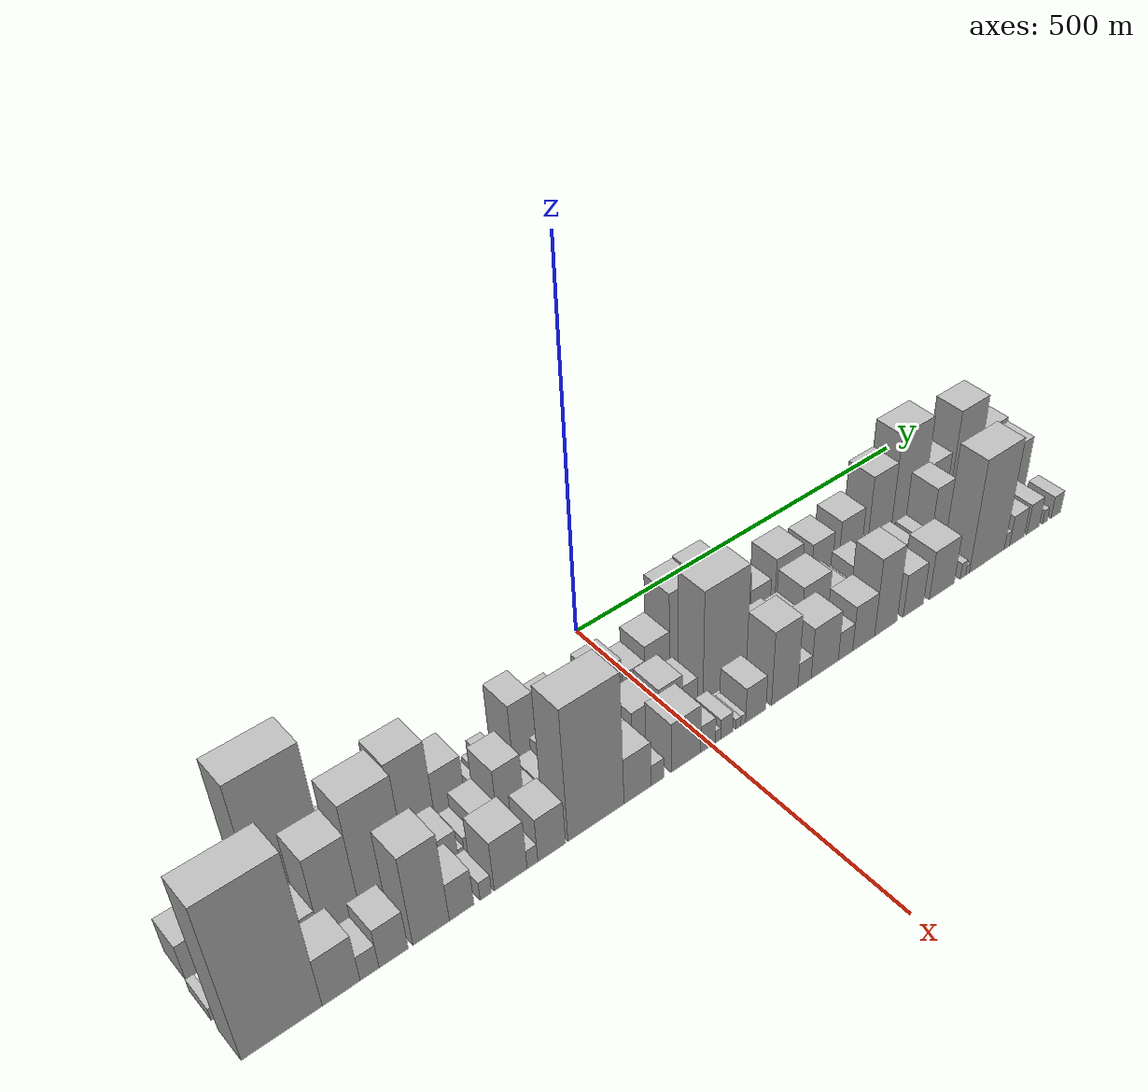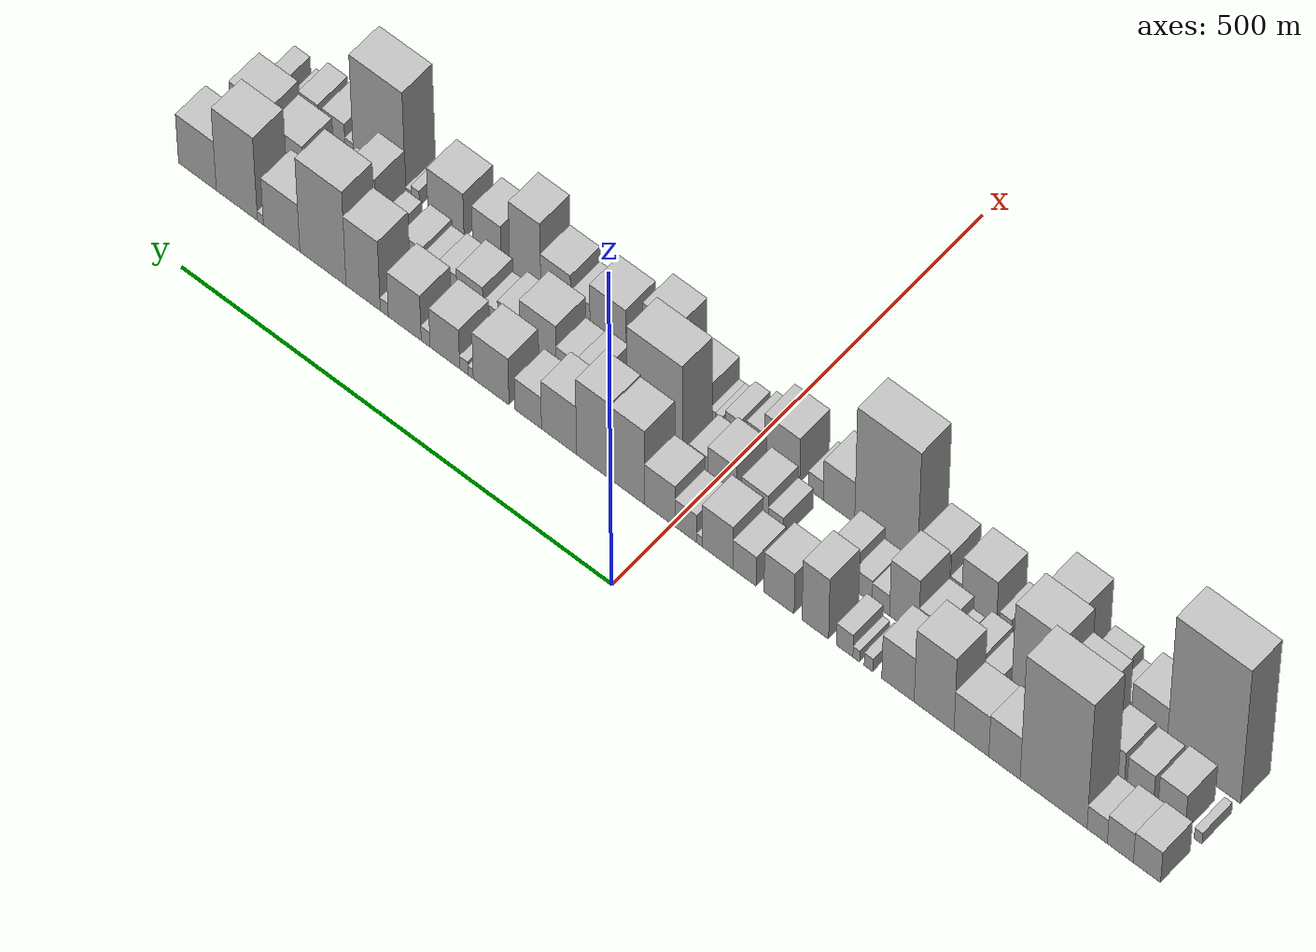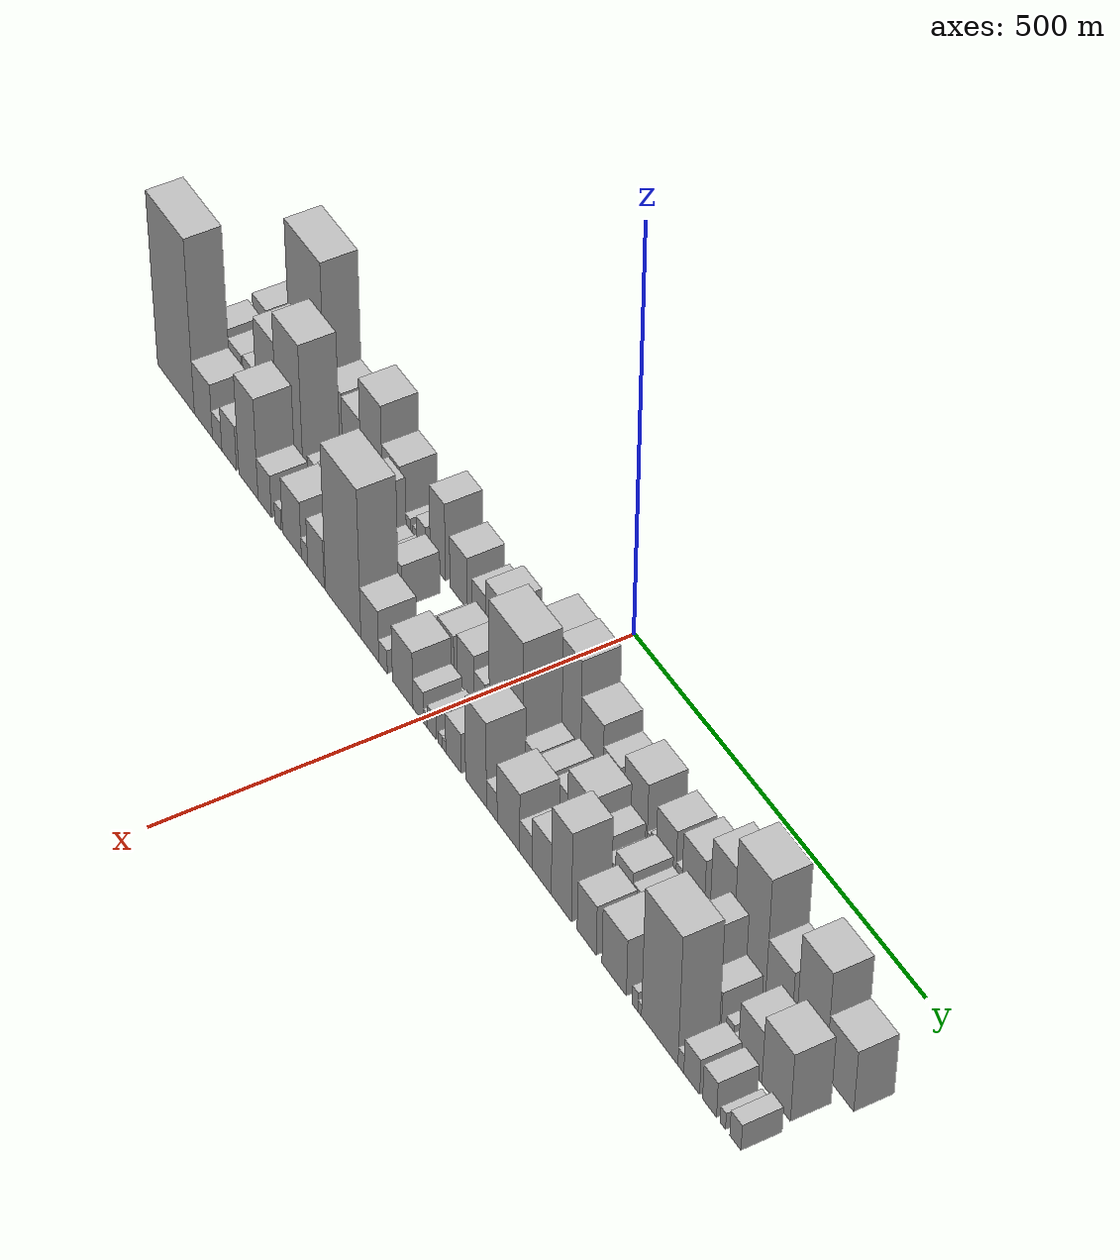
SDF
<sdf version="1.6">
 <world name="default">
  <scene>
   <sky><clouds><speed>12</speed></clouds></sky>
   <ambient>0.4 0.4 0.4 1</ambient>
   <background>0.7 0.7 0.7 1</background>
   <shadows>1</shadows>
  </scene>
  <gravity>0 0 -9.8066</gravity>
  <magnetic_field>6e-06 2.3e-05 -4.2e-05</magnetic_field>
  <physics default="0" name="default_physics" type="ode">
   <ode>
    <solver>
     <type>quick</type>
     <iters>10</iters>
     <sor>1.0</sor>
     <use_dynamic_moi_rescaling>0</use_dynamic_moi_rescaling>
    </solver>
    <constraints>
     <cfm>0</cfm>
     <erp>0.2</erp>
     <contact_max_correcting_vel>100</contact_max_correcting_vel>
     <contact_surface_layer>0.001</contact_surface_layer>
    </constraints>
   </ode>
   <max_step_size>0.004</max_step_size>
   <real_time_factor>1</real_time_factor>
   <real_time_update_rate>250</real_time_update_rate>
  </physics>
  <light name="sun" type="directional">
   <pose>0 0 10 0 0 0</pose>
   <diffuse>0.8 0.8 0.8 1</diffuse>
   <specular>0.2 0.2 0.2 1</specular>
   <attenuation>
    <range>1000</range>
    <constant>0.9</constant>
    <linear>0.01</linear>
    <quadratic>0.001</quadratic>
   </attenuation>
   <direction>-0.5 0.1 -0.9</direction>
  </light>
  <model name="building_1">
   <static>1</static>
   <pose>100.0000 -530.0485 0 0.000000 0.000000 0.000000</pose>
   <link name="link">
    <pose>0 0 25.50 0 0 0</pose>
    <collision name="collision"><geometry><box><size>40.0000 29.9029 51.0000</size></box></geometry></collision>
    <visual name="visual">
     <cast_shadows>0</cast_shadows>
     <geometry><box><size>40.0000 29.9029 51.0000</size></box></geometry>
     <material>
      <script>
       <uri>model://HANNAS_wall/materials/scripts</uri>
       <uri>model://HANNAS_wall/materials/textures</uri>
       <name>vrc/HANNAS_wall</name>
      </script>
     </material>
    </visual>
   </link>
  </model>
  <model name="building_2">
   <static>1</static>
   <pose>100.0000 -500.7562 0 0.000000 0.000000 0.000000</pose>
   <link name="link">
    <pose>0 0 24.00 0 0 0</pose>
    <collision name="collision"><geometry><box><size>40.0000 28.6818 48.0000</size></box></geometry></collision>
    <visual name="visual">
     <cast_shadows>0</cast_shadows>
     <geometry><box><size>40.0000 28.6818 48.0000</size></box></geometry>
     <material>
      <script>
       <uri>model://HANNAS_wall/materials/scripts</uri>
       <uri>model://HANNAS_wall/materials/textures</uri>
       <name>vrc/HANNAS_wall</name>
      </script>
     </material>
    </visual>
   </link>
  </model>
  <model name="building_3">
   <static>1</static>
   <pose>100.0000 -475.2636 0 0.000000 0.000000 0.000000</pose>
   <link name="link">
    <pose>0 0 19.50 0 0 0</pose>
    <collision name="collision"><geometry><box><size>40.0000 22.3033 39.0000</size></box></geometry></collision>
    <visual name="visual">
     <cast_shadows>0</cast_shadows>
     <geometry><box><size>40.0000 22.3033 39.0000</size></box></geometry>
     <material>
      <script>
       <uri>model://HANNAS_wall/materials/scripts</uri>
       <uri>model://HANNAS_wall/materials/textures</uri>
       <name>vrc/HANNAS_wall</name>
      </script>
     </material>
    </visual>
   </link>
  </model>
  <model name="building_4">
   <static>1</static>
   <pose>100.0000 -427.1443 0 0.000000 0.000000 0.000000</pose>
   <link name="link">
    <pose>0 0 103.50 0 0 0</pose>
    <collision name="collision"><geometry><box><size>40.0000 73.9355 207.0000</size></box></geometry></collision>
    <visual name="visual">
     <cast_shadows>0</cast_shadows>
     <geometry><box><size>40.0000 73.9355 207.0000</size></box></geometry>
     <material>
      <script>
       <uri>model://HANNAS_wall/materials/scripts</uri>
       <uri>model://HANNAS_wall/materials/textures</uri>
       <name>vrc/HANNAS_wall</name>
      </script>
     </material>
    </visual>
   </link>
  </model>
  <model name="building_5">
   <static>1</static>
   <pose>100.0000 -372.8234 0 0.000000 0.000000 0.000000</pose>
   <link name="link">
    <pose>0 0 34.50 0 0 0</pose>
    <collision name="collision"><geometry><box><size>40.0000 34.7063 69.0000</size></box></geometry></collision>
    <visual name="visual">
     <cast_shadows>0</cast_shadows>
     <geometry><box><size>40.0000 34.7063 69.0000</size></box></geometry>
     <material>
      <script>
       <uri>model://HANNAS_wall/materials/scripts</uri>
       <uri>model://HANNAS_wall/materials/textures</uri>
       <name>vrc/HANNAS_wall</name>
      </script>
     </material>
    </visual>
   </link>
  </model>
  <model name="building_6">
   <static>1</static>
   <pose>100.0000 -336.1685 0 0.000000 0.000000 0.000000</pose>
   <link name="link">
    <pose>0 0 33.00 0 0 0</pose>
    <collision name="collision"><geometry><box><size>40.0000 38.6033 66.0000</size></box></geometry></collision>
    <visual name="visual">
     <cast_shadows>0</cast_shadows>
     <geometry><box><size>40.0000 38.6033 66.0000</size></box></geometry>
     <material>
      <script>
       <uri>model://HANNAS_wall/materials/scripts</uri>
       <uri>model://HANNAS_wall/materials/textures</uri>
       <name>vrc/HANNAS_wall</name>
      </script>
     </material>
    </visual>
   </link>
  </model>
  <model name="building_7">
   <static>1</static>
   <pose>100.0000 -294.6221 0 0.000000 0.000000 0.000000</pose>
   <link name="link">
    <pose>0 0 60.00 0 0 0</pose>
    <collision name="collision"><geometry><box><size>40.0000 44.4894 120.0000</size></box></geometry></collision>
    <visual name="visual">
     <cast_shadows>0</cast_shadows>
     <geometry><box><size>40.0000 44.4894 120.0000</size></box></geometry>
     <material>
      <script>
       <uri>model://HANNAS_wall/materials/scripts</uri>
       <uri>model://HANNAS_wall/materials/textures</uri>
       <name>vrc/HANNAS_wall</name>
      </script>
     </material>
    </visual>
   </link>
  </model>
  <model name="building_8">
   <static>1</static>
   <pose>100.0000 -254.2661 0 0.000000 0.000000 0.000000</pose>
   <link name="link">
    <pose>0 0 36.00 0 0 0</pose>
    <collision name="collision"><geometry><box><size>40.0000 36.2226 72.0000</size></box></geometry></collision>
    <visual name="visual">
     <cast_shadows>0</cast_shadows>
     <geometry><box><size>40.0000 36.2226 72.0000</size></box></geometry>
     <material>
      <script>
       <uri>model://HANNAS_wall/materials/scripts</uri>
       <uri>model://HANNAS_wall/materials/textures</uri>
       <name>vrc/HANNAS_wall</name>
      </script>
     </material>
    </visual>
   </link>
  </model>
  <model name="building_9">
   <static>1</static>
   <pose>100.0000 -221.3001 0 0.000000 0.000000 0.000000</pose>
   <link name="link">
    <pose>0 0 10.50 0 0 0</pose>
    <collision name="collision"><geometry><box><size>40.0000 9.7096 21.0000</size></box></geometry></collision>
    <visual name="visual">
     <cast_shadows>0</cast_shadows>
     <geometry><box><size>40.0000 9.7096 21.0000</size></box></geometry>
     <material>
      <script>
       <uri>model://HANNAS_wall/materials/scripts</uri>
       <uri>model://HANNAS_wall/materials/textures</uri>
       <name>vrc/HANNAS_wall</name>
      </script>
     </material>
    </visual>
   </link>
  </model>
  <model name="building_10">
   <static>1</static>
   <pose>100.0000 -207.6392 0 0.000000 0.000000 0.000000</pose>
   <link name="link">
    <pose>0 0 9.00 0 0 0</pose>
    <collision name="collision"><geometry><box><size>40.0000 7.6121 18.0000</size></box></geometry></collision>
    <visual name="visual">
     <cast_shadows>0</cast_shadows>
     <geometry><box><size>40.0000 7.6121 18.0000</size></box></geometry>
     <material>
      <script>
       <uri>model://HANNAS_wall/materials/scripts</uri>
       <uri>model://HANNAS_wall/materials/textures</uri>
       <name>vrc/HANNAS_wall</name>
      </script>
     </material>
    </visual>
   </link>
  </model>
  <model name="building_11">
   <static>1</static>
   <pose>100.0000 -194.6576 0 0.000000 0.000000 0.000000</pose>
   <link name="link">
    <pose>0 0 18.00 0 0 0</pose>
    <collision name="collision"><geometry><box><size>40.0000 18.3511 36.0000</size></box></geometry></collision>
    <visual name="visual">
     <cast_shadows>0</cast_shadows>
     <geometry><box><size>40.0000 18.3511 36.0000</size></box></geometry>
     <material>
      <script>
       <uri>model://HANNAS_wall/materials/scripts</uri>
       <uri>model://HANNAS_wall/materials/textures</uri>
       <name>vrc/HANNAS_wall</name>
      </script>
     </material>
    </visual>
   </link>
  </model>
  <model name="building_12">
   <static>1</static>
   <pose>100.0000 -161.5539 0 0.000000 0.000000 0.000000</pose>
   <link name="link">
    <pose>0 0 49.50 0 0 0</pose>
    <collision name="collision"><geometry><box><size>40.0000 29.8562 99.0000</size></box></geometry></collision>
    <visual name="visual">
     <cast_shadows>0</cast_shadows>
     <geometry><box><size>40.0000 29.8562 99.0000</size></box></geometry>
     <material>
      <script>
       <uri>model://HANNAS_wall/materials/scripts</uri>
       <uri>model://HANNAS_wall/materials/textures</uri>
       <name>vrc/HANNAS_wall</name>
      </script>
     </material>
    </visual>
   </link>
  </model>
  <model name="building_13">
   <static>1</static>
   <pose>100.0000 -120.6561 0 0.000000 0.000000 0.000000</pose>
   <link name="link">
    <pose>0 0 33.00 0 0 0</pose>
    <collision name="collision"><geometry><box><size>40.0000 33.9394 66.0000</size></box></geometry></collision>
    <visual name="visual">
     <cast_shadows>0</cast_shadows>
     <geometry><box><size>40.0000 33.9394 66.0000</size></box></geometry>
     <material>
      <script>
       <uri>model://HANNAS_wall/materials/scripts</uri>
       <uri>model://HANNAS_wall/materials/textures</uri>
       <name>vrc/HANNAS_wall</name>
      </script>
     </material>
    </visual>
   </link>
  </model>
  <model name="building_14">
   <static>1</static>
   <pose>100.0000 -81.5072 0 0.000000 0.000000 0.000000</pose>
   <link name="link">
    <pose>0 0 24.00 0 0 0</pose>
    <collision name="collision"><geometry><box><size>40.0000 26.3584 48.0000</size></box></geometry></collision>
    <visual name="visual">
     <cast_shadows>0</cast_shadows>
     <geometry><box><size>40.0000 26.3584 48.0000</size></box></geometry>
     <material>
      <script>
       <uri>model://HANNAS_wall/materials/scripts</uri>
       <uri>model://HANNAS_wall/materials/textures</uri>
       <name>vrc/HANNAS_wall</name>
      </script>
     </material>
    </visual>
   </link>
  </model>
  <model name="building_15">
   <static>1</static>
   <pose>100.0000 -50.8605 0 0.000000 0.000000 0.000000</pose>
   <link name="link">
    <pose>0 0 34.50 0 0 0</pose>
    <collision name="collision"><geometry><box><size>40.0000 34.9350 69.0000</size></box></geometry></collision>
    <visual name="visual">
     <cast_shadows>0</cast_shadows>
     <geometry><box><size>40.0000 34.9350 69.0000</size></box></geometry>
     <material>
      <script>
       <uri>model://HANNAS_wall/materials/scripts</uri>
       <uri>model://HANNAS_wall/materials/textures</uri>
       <name>vrc/HANNAS_wall</name>
      </script>
     </material>
    </visual>
   </link>
  </model>
  <model name="building_16">
   <static>1</static>
   <pose>100.0000 -30.2823 0 0.000000 0.000000 0.000000</pose>
   <link name="link">
    <pose>0 0 7.50 0 0 0</pose>
    <collision name="collision"><geometry><box><size>40.0000 6.2215 15.0000</size></box></geometry></collision>
    <visual name="visual">
     <cast_shadows>0</cast_shadows>
     <geometry><box><size>40.0000 6.2215 15.0000</size></box></geometry>
     <material>
      <script>
       <uri>model://HANNAS_wall/materials/scripts</uri>
       <uri>model://HANNAS_wall/materials/textures</uri>
       <name>vrc/HANNAS_wall</name>
      </script>
     </material>
    </visual>
   </link>
  </model>
  <model name="building_17">
   <static>1</static>
   <pose>100.0000 -14.8061 0 0.000000 0.000000 0.000000</pose>
   <link name="link">
    <pose>0 0 22.50 0 0 0</pose>
    <collision name="collision"><geometry><box><size>40.0000 24.7308 45.0000</size></box></geometry></collision>
    <visual name="visual">
     <cast_shadows>0</cast_shadows>
     <geometry><box><size>40.0000 24.7308 45.0000</size></box></geometry>
     <material>
      <script>
       <uri>model://HANNAS_wall/materials/scripts</uri>
       <uri>model://HANNAS_wall/materials/textures</uri>
       <name>vrc/HANNAS_wall</name>
      </script>
     </material>
    </visual>
   </link>
  </model>
  <model name="building_18">
   <static>1</static>
   <pose>100.0000 14.7597 0 0.000000 0.000000 0.000000</pose>
   <link name="link">
    <pose>0 0 33.00 0 0 0</pose>
    <collision name="collision"><geometry><box><size>40.0000 34.4009 66.0000</size></box></geometry></collision>
    <visual name="visual">
     <cast_shadows>0</cast_shadows>
     <geometry><box><size>40.0000 34.4009 66.0000</size></box></geometry>
     <material>
      <script>
       <uri>model://HANNAS_wall/materials/scripts</uri>
       <uri>model://HANNAS_wall/materials/textures</uri>
       <name>vrc/HANNAS_wall</name>
      </script>
     </material>
    </visual>
   </link>
  </model>
  <model name="building_19">
   <static>1</static>
   <pose>100.0000 51.3344 0 0.000000 0.000000 0.000000</pose>
   <link name="link">
    <pose>0 0 60.00 0 0 0</pose>
    <collision name="collision"><geometry><box><size>40.0000 38.7485 120.0000</size></box></geometry></collision>
    <visual name="visual">
     <cast_shadows>0</cast_shadows>
     <geometry><box><size>40.0000 38.7485 120.0000</size></box></geometry>
     <material>
      <script>
       <uri>model://HANNAS_wall/materials/scripts</uri>
       <uri>model://HANNAS_wall/materials/textures</uri>
       <name>vrc/HANNAS_wall</name>
      </script>
     </material>
    </visual>
   </link>
  </model>
  <model name="building_20">
   <static>1</static>
   <pose>100.0000 90.4751 0 0.000000 0.000000 0.000000</pose>
   <link name="link">
    <pose>0 0 61.50 0 0 0</pose>
    <collision name="collision"><geometry><box><size>40.0000 39.5329 123.0000</size></box></geometry></collision>
    <visual name="visual">
     <cast_shadows>0</cast_shadows>
     <geometry><box><size>40.0000 39.5329 123.0000</size></box></geometry>
     <material>
      <script>
       <uri>model://HANNAS_wall/materials/scripts</uri>
       <uri>model://HANNAS_wall/materials/textures</uri>
       <name>vrc/HANNAS_wall</name>
      </script>
     </material>
    </visual>
   </link>
  </model>
  <model name="building_21">
   <static>1</static>
   <pose>100.0000 130.3828 0 0.000000 0.000000 0.000000</pose>
   <link name="link">
    <pose>0 0 39.00 0 0 0</pose>
    <collision name="collision"><geometry><box><size>40.0000 40.2824 78.0000</size></box></geometry></collision>
    <visual name="visual">
     <cast_shadows>0</cast_shadows>
     <geometry><box><size>40.0000 40.2824 78.0000</size></box></geometry>
     <material>
      <script>
       <uri>model://HANNAS_wall/materials/scripts</uri>
       <uri>model://HANNAS_wall/materials/textures</uri>
       <name>vrc/HANNAS_wall</name>
      </script>
     </material>
    </visual>
   </link>
  </model>
  <model name="building_22">
   <static>1</static>
   <pose>100.0000 165.8007 0 0.000000 0.000000 0.000000</pose>
   <link name="link">
    <pose>0 0 25.50 0 0 0</pose>
    <collision name="collision"><geometry><box><size>40.0000 30.5533 51.0000</size></box></geometry></collision>
    <visual name="visual">
     <cast_shadows>0</cast_shadows>
     <geometry><box><size>40.0000 30.5533 51.0000</size></box></geometry>
     <material>
      <script>
       <uri>model://HANNAS_wall/materials/scripts</uri>
       <uri>model://HANNAS_wall/materials/textures</uri>
       <name>vrc/HANNAS_wall</name>
      </script>
     </material>
    </visual>
   </link>
  </model>
  <model name="building_23">
   <static>1</static>
   <pose>100.0000 208.7580 0 0.000000 0.000000 0.000000</pose>
   <link name="link">
    <pose>0 0 37.50 0 0 0</pose>
    <collision name="collision"><geometry><box><size>40.0000 41.3613 75.0000</size></box></geometry></collision>
    <visual name="visual">
     <cast_shadows>0</cast_shadows>
     <geometry><box><size>40.0000 41.3613 75.0000</size></box></geometry>
     <material>
      <script>
       <uri>model://HANNAS_wall/materials/scripts</uri>
       <uri>model://HANNAS_wall/materials/textures</uri>
       <name>vrc/HANNAS_wall</name>
      </script>
     </material>
    </visual>
   </link>
  </model>
  <model name="building_24">
   <static>1</static>
   <pose>100.0000 232.5239 0 0.000000 0.000000 0.000000</pose>
   <link name="link">
    <pose>0 0 7.50 0 0 0</pose>
    <collision name="collision"><geometry><box><size>40.0000 6.1706 15.0000</size></box></geometry></collision>
    <visual name="visual">
     <cast_shadows>0</cast_shadows>
     <geometry><box><size>40.0000 6.1706 15.0000</size></box></geometry>
     <material>
      <script>
       <uri>model://HANNAS_wall/materials/scripts</uri>
       <uri>model://HANNAS_wall/materials/textures</uri>
       <name>vrc/HANNAS_wall</name>
      </script>
     </material>
    </visual>
   </link>
  </model>
  <model name="building_25">
   <static>1</static>
   <pose>100.0000 240.3950 0 0.000000 0.000000 0.000000</pose>
   <link name="link">
    <pose>0 0 10.50 0 0 0</pose>
    <collision name="collision"><geometry><box><size>40.0000 9.5717 21.0000</size></box></geometry></collision>
    <visual name="visual">
     <cast_shadows>0</cast_shadows>
     <geometry><box><size>40.0000 9.5717 21.0000</size></box></geometry>
     <material>
      <script>
       <uri>model://HANNAS_wall/materials/scripts</uri>
       <uri>model://HANNAS_wall/materials/textures</uri>
       <name>vrc/HANNAS_wall</name>
      </script>
     </material>
    </visual>
   </link>
  </model>
  <model name="building_26">
   <static>1</static>
   <pose>100.0000 262.4223 0 0.000000 0.000000 0.000000</pose>
   <link name="link">
    <pose>0 0 31.50 0 0 0</pose>
    <collision name="collision"><geometry><box><size>40.0000 34.4828 63.0000</size></box></geometry></collision>
    <visual name="visual">
     <cast_shadows>0</cast_shadows>
     <geometry><box><size>40.0000 34.4828 63.0000</size></box></geometry>
     <material>
      <script>
       <uri>model://HANNAS_wall/materials/scripts</uri>
       <uri>model://HANNAS_wall/materials/textures</uri>
       <name>vrc/HANNAS_wall</name>
      </script>
     </material>
    </visual>
   </link>
  </model>
  <model name="building_27">
   <static>1</static>
   <pose>100.0000 284.8369 0 0.000000 0.000000 0.000000</pose>
   <link name="link">
    <pose>0 0 12.00 0 0 0</pose>
    <collision name="collision"><geometry><box><size>40.0000 10.3464 24.0000</size></box></geometry></collision>
    <visual name="visual">
     <cast_shadows>0</cast_shadows>
     <geometry><box><size>40.0000 10.3464 24.0000</size></box></geometry>
     <material>
      <script>
       <uri>model://HANNAS_wall/materials/scripts</uri>
       <uri>model://HANNAS_wall/materials/textures</uri>
       <name>vrc/HANNAS_wall</name>
      </script>
     </material>
    </visual>
   </link>
  </model>
  <model name="building_28">
   <static>1</static>
   <pose>100.0000 309.1547 0 0.000000 0.000000 0.000000</pose>
   <link name="link">
    <pose>0 0 36.00 0 0 0</pose>
    <collision name="collision"><geometry><box><size>40.0000 38.2892 72.0000</size></box></geometry></collision>
    <visual name="visual">
     <cast_shadows>0</cast_shadows>
     <geometry><box><size>40.0000 38.2892 72.0000</size></box></geometry>
     <material>
      <script>
       <uri>model://HANNAS_wall/materials/scripts</uri>
       <uri>model://HANNAS_wall/materials/textures</uri>
       <name>vrc/HANNAS_wall</name>
      </script>
     </material>
    </visual>
   </link>
  </model>
  <model name="building_29">
   <static>1</static>
   <pose>100.0000 332.9960 0 0.000000 0.000000 0.000000</pose>
   <link name="link">
    <pose>0 0 10.50 0 0 0</pose>
    <collision name="collision"><geometry><box><size>40.0000 9.3933 21.0000</size></box></geometry></collision>
    <visual name="visual">
     <cast_shadows>0</cast_shadows>
     <geometry><box><size>40.0000 9.3933 21.0000</size></box></geometry>
     <material>
      <script>
       <uri>model://HANNAS_wall/materials/scripts</uri>
       <uri>model://HANNAS_wall/materials/textures</uri>
       <name>vrc/HANNAS_wall</name>
      </script>
     </material>
    </visual>
   </link>
  </model>
  <model name="building_30">
   <static>1</static>
   <pose>100.0000 357.7204 0 0.000000 0.000000 0.000000</pose>
   <link name="link">
    <pose>0 0 55.50 0 0 0</pose>
    <collision name="collision"><geometry><box><size>40.0000 40.0556 111.0000</size></box></geometry></collision>
    <visual name="visual">
     <cast_shadows>0</cast_shadows>
     <geometry><box><size>40.0000 40.0556 111.0000</size></box></geometry>
     <material>
      <script>
       <uri>model://HANNAS_wall/materials/scripts</uri>
       <uri>model://HANNAS_wall/materials/textures</uri>
       <name>vrc/HANNAS_wall</name>
      </script>
     </material>
    </visual>
   </link>
  </model>
  <model name="building_31">
   <static>1</static>
   <pose>100.0000 404.8930 0 0.000000 0.000000 0.000000</pose>
   <link name="link">
    <pose>0 0 75.00 0 0 0</pose>
    <collision name="collision"><geometry><box><size>40.0000 54.2895 150.0000</size></box></geometry></collision>
    <visual name="visual">
     <cast_shadows>0</cast_shadows>
     <geometry><box><size>40.0000 54.2895 150.0000</size></box></geometry>
     <material>
      <script>
       <uri>model://HANNAS_wall/materials/scripts</uri>
       <uri>model://HANNAS_wall/materials/textures</uri>
       <name>vrc/HANNAS_wall</name>
      </script>
     </material>
    </visual>
   </link>
  </model>
  <model name="building_32">
   <static>1</static>
   <pose>100.0000 453.5138 0 0.000000 0.000000 0.000000</pose>
   <link name="link">
    <pose>0 0 37.50 0 0 0</pose>
    <collision name="collision"><geometry><box><size>40.0000 42.9522 75.0000</size></box></geometry></collision>
    <visual name="visual">
     <cast_shadows>0</cast_shadows>
     <geometry><box><size>40.0000 42.9522 75.0000</size></box></geometry>
     <material>
      <script>
       <uri>model://HANNAS_wall/materials/scripts</uri>
       <uri>model://HANNAS_wall/materials/textures</uri>
       <name>vrc/HANNAS_wall</name>
      </script>
     </material>
    </visual>
   </link>
  </model>
  <model name="building_33">
   <static>1</static>
   <pose>100.0000 478.4617 0 0.000000 0.000000 0.000000</pose>
   <link name="link">
    <pose>0 0 7.50 0 0 0</pose>
    <collision name="collision"><geometry><box><size>40.0000 6.9436 15.0000</size></box></geometry></collision>
    <visual name="visual">
     <cast_shadows>0</cast_shadows>
     <geometry><box><size>40.0000 6.9436 15.0000</size></box></geometry>
     <material>
      <script>
       <uri>model://HANNAS_wall/materials/scripts</uri>
       <uri>model://HANNAS_wall/materials/textures</uri>
       <name>vrc/HANNAS_wall</name>
      </script>
     </material>
    </visual>
   </link>
  </model>
  <model name="building_34">
   <static>1</static>
   <pose>100.0000 506.3013 0 0.000000 0.000000 0.000000</pose>
   <link name="link">
    <pose>0 0 66.00 0 0 0</pose>
    <collision name="collision"><geometry><box><size>40.0000 48.7356 132.0000</size></box></geometry></collision>
    <visual name="visual">
     <cast_shadows>0</cast_shadows>
     <geometry><box><size>40.0000 48.7356 132.0000</size></box></geometry>
     <material>
      <script>
       <uri>model://HANNAS_wall/materials/scripts</uri>
       <uri>model://HANNAS_wall/materials/textures</uri>
       <name>vrc/HANNAS_wall</name>
      </script>
     </material>
    </visual>
   </link>
  </model>
  <model name="building_35">
   <static>1</static>
   <pose>100.0000 552.9983 0 0.000000 0.000000 0.000000</pose>
   <link name="link">
    <pose>0 0 39.00 0 0 0</pose>
    <collision name="collision"><geometry><box><size>40.0000 44.6583 78.0000</size></box></geometry></collision>
    <visual name="visual">
     <cast_shadows>0</cast_shadows>
     <geometry><box><size>40.0000 44.6583 78.0000</size></box></geometry>
     <material>
      <script>
       <uri>model://HANNAS_wall/materials/scripts</uri>
       <uri>model://HANNAS_wall/materials/textures</uri>
       <name>vrc/HANNAS_wall</name>
      </script>
     </material>
    </visual>
   </link>
  </model>
  <model name="building_36">
   <static>1</static>
   <pose>152.0000 -543.7004 0 0.000000 0.000000 0.000000</pose>
   <link name="link">
    <pose>0 0 9.00 0 0 0</pose>
    <collision name="collision"><geometry><box><size>40.0000 8.5993 18.0000</size></box></geometry></collision>
    <visual name="visual">
     <cast_shadows>0</cast_shadows>
     <geometry><box><size>40.0000 8.5993 18.0000</size></box></geometry>
     <material>
      <script>
       <uri>model://HANNAS_wall/materials/scripts</uri>
       <uri>model://HANNAS_wall/materials/textures</uri>
       <name>vrc/HANNAS_wall</name>
      </script>
     </material>
    </visual>
   </link>
  </model>
  <model name="building_37">
   <static>1</static>
   <pose>152.0000 -514.3517 0 0.000000 0.000000 0.000000</pose>
   <link name="link">
    <pose>0 0 30.00 0 0 0</pose>
    <collision name="collision"><geometry><box><size>40.0000 30.0981 60.0000</size></box></geometry></collision>
    <visual name="visual">
     <cast_shadows>0</cast_shadows>
     <geometry><box><size>40.0000 30.0981 60.0000</size></box></geometry>
     <material>
      <script>
       <uri>model://HANNAS_wall/materials/scripts</uri>
       <uri>model://HANNAS_wall/materials/textures</uri>
       <name>vrc/HANNAS_wall</name>
      </script>
     </material>
    </visual>
   </link>
  </model>
  <model name="building_38">
   <static>1</static>
   <pose>152.0000 -479.7937 0 0.000000 0.000000 0.000000</pose>
   <link name="link">
    <pose>0 0 27.00 0 0 0</pose>
    <collision name="collision"><geometry><box><size>40.0000 29.0178 54.0000</size></box></geometry></collision>
    <visual name="visual">
     <cast_shadows>0</cast_shadows>
     <geometry><box><size>40.0000 29.0178 54.0000</size></box></geometry>
     <material>
      <script>
       <uri>model://HANNAS_wall/materials/scripts</uri>
       <uri>model://HANNAS_wall/materials/textures</uri>
       <name>vrc/HANNAS_wall</name>
      </script>
     </material>
    </visual>
   </link>
  </model>
  <model name="building_39">
   <static>1</static>
   <pose>152.0000 -447.8820 0 0.000000 0.000000 0.000000</pose>
   <link name="link">
    <pose>0 0 28.50 0 0 0</pose>
    <collision name="collision"><geometry><box><size>40.0000 28.8056 57.0000</size></box></geometry></collision>
    <visual name="visual">
     <cast_shadows>0</cast_shadows>
     <geometry><box><size>40.0000 28.8056 57.0000</size></box></geometry>
     <material>
      <script>
       <uri>model://HANNAS_wall/materials/scripts</uri>
       <uri>model://HANNAS_wall/materials/textures</uri>
       <name>vrc/HANNAS_wall</name>
      </script>
     </material>
    </visual>
   </link>
  </model>
  <model name="building_40">
   <static>1</static>
   <pose>152.0000 -411.9997 0 0.000000 0.000000 0.000000</pose>
   <link name="link">
    <pose>0 0 64.50 0 0 0</pose>
    <collision name="collision"><geometry><box><size>40.0000 42.9589 129.0000</size></box></geometry></collision>
    <visual name="visual">
     <cast_shadows>0</cast_shadows>
     <geometry><box><size>40.0000 42.9589 129.0000</size></box></geometry>
     <material>
      <script>
       <uri>model://HANNAS_wall/materials/scripts</uri>
       <uri>model://HANNAS_wall/materials/textures</uri>
       <name>vrc/HANNAS_wall</name>
      </script>
     </material>
    </visual>
   </link>
  </model>
  <model name="building_41">
   <static>1</static>
   <pose>152.0000 -363.5714 0 0.000000 0.000000 0.000000</pose>
   <link name="link">
    <pose>0 0 84.00 0 0 0</pose>
    <collision name="collision"><geometry><box><size>40.0000 53.8978 168.0000</size></box></geometry></collision>
    <visual name="visual">
     <cast_shadows>0</cast_shadows>
     <geometry><box><size>40.0000 53.8978 168.0000</size></box></geometry>
     <material>
      <script>
       <uri>model://HANNAS_wall/materials/scripts</uri>
       <uri>model://HANNAS_wall/materials/textures</uri>
       <name>vrc/HANNAS_wall</name>
      </script>
     </material>
    </visual>
   </link>
  </model>
  <model name="building_42">
   <static>1</static>
   <pose>152.0000 -315.9194 0 0.000000 0.000000 0.000000</pose>
   <link name="link">
    <pose>0 0 18.00 0 0 0</pose>
    <collision name="collision"><geometry><box><size>40.0000 21.4063 36.0000</size></box></geometry></collision>
    <visual name="visual">
     <cast_shadows>0</cast_shadows>
     <geometry><box><size>40.0000 21.4063 36.0000</size></box></geometry>
     <material>
      <script>
       <uri>model://HANNAS_wall/materials/scripts</uri>
       <uri>model://HANNAS_wall/materials/textures</uri>
       <name>vrc/HANNAS_wall</name>
      </script>
     </material>
    </visual>
   </link>
  </model>
  <model name="building_43">
   <static>1</static>
   <pose>152.0000 -293.4636 0 0.000000 0.000000 0.000000</pose>
   <link name="link">
    <pose>0 0 22.50 0 0 0</pose>
    <collision name="collision"><geometry><box><size>40.0000 23.5053 45.0000</size></box></geometry></collision>
    <visual name="visual">
     <cast_shadows>0</cast_shadows>
     <geometry><box><size>40.0000 23.5053 45.0000</size></box></geometry>
     <material>
      <script>
       <uri>model://HANNAS_wall/materials/scripts</uri>
       <uri>model://HANNAS_wall/materials/textures</uri>
       <name>vrc/HANNAS_wall</name>
      </script>
     </material>
    </visual>
   </link>
  </model>
  <model name="building_44">
   <static>1</static>
   <pose>152.0000 -278.1289 0 0.000000 0.000000 0.000000</pose>
   <link name="link">
    <pose>0 0 7.50 0 0 0</pose>
    <collision name="collision"><geometry><box><size>40.0000 7.1641 15.0000</size></box></geometry></collision>
    <visual name="visual">
     <cast_shadows>0</cast_shadows>
     <geometry><box><size>40.0000 7.1641 15.0000</size></box></geometry>
     <material>
      <script>
       <uri>model://HANNAS_wall/materials/scripts</uri>
       <uri>model://HANNAS_wall/materials/textures</uri>
       <name>vrc/HANNAS_wall</name>
      </script>
     </material>
    </visual>
   </link>
  </model>
  <model name="building_45">
   <static>1</static>
   <pose>152.0000 -268.0411 0 0.000000 0.000000 0.000000</pose>
   <link name="link">
    <pose>0 0 13.50 0 0 0</pose>
    <collision name="collision"><geometry><box><size>40.0000 13.0114 27.0000</size></box></geometry></collision>
    <visual name="visual">
     <cast_shadows>0</cast_shadows>
     <geometry><box><size>40.0000 13.0114 27.0000</size></box></geometry>
     <material>
      <script>
       <uri>model://HANNAS_wall/materials/scripts</uri>
       <uri>model://HANNAS_wall/materials/textures</uri>
       <name>vrc/HANNAS_wall</name>
      </script>
     </material>
    </visual>
   </link>
  </model>
  <model name="building_46">
   <static>1</static>
   <pose>152.0000 -247.6543 0 0.000000 0.000000 0.000000</pose>
   <link name="link">
    <pose>0 0 24.00 0 0 0</pose>
    <collision name="collision"><geometry><box><size>40.0000 27.7624 48.0000</size></box></geometry></collision>
    <visual name="visual">
     <cast_shadows>0</cast_shadows>
     <geometry><box><size>40.0000 27.7624 48.0000</size></box></geometry>
     <material>
      <script>
       <uri>model://HANNAS_wall/materials/scripts</uri>
       <uri>model://HANNAS_wall/materials/textures</uri>
       <name>vrc/HANNAS_wall</name>
      </script>
     </material>
    </visual>
   </link>
  </model>
  <model name="building_47">
   <static>1</static>
   <pose>152.0000 -217.5060 0 0.000000 0.000000 0.000000</pose>
   <link name="link">
    <pose>0 0 46.50 0 0 0</pose>
    <collision name="collision"><geometry><box><size>40.0000 32.5342 93.0000</size></box></geometry></collision>
    <visual name="visual">
     <cast_shadows>0</cast_shadows>
     <geometry><box><size>40.0000 32.5342 93.0000</size></box></geometry>
     <material>
      <script>
       <uri>model://HANNAS_wall/materials/scripts</uri>
       <uri>model://HANNAS_wall/materials/textures</uri>
       <name>vrc/HANNAS_wall</name>
      </script>
     </material>
    </visual>
   </link>
  </model>
  <model name="building_48">
   <static>1</static>
   <pose>152.0000 -191.4395 0 0.000000 0.000000 0.000000</pose>
   <link name="link">
    <pose>0 0 16.50 0 0 0</pose>
    <collision name="collision"><geometry><box><size>40.0000 19.5988 33.0000</size></box></geometry></collision>
    <visual name="visual">
     <cast_shadows>0</cast_shadows>
     <geometry><box><size>40.0000 19.5988 33.0000</size></box></geometry>
     <material>
      <script>
       <uri>model://HANNAS_wall/materials/scripts</uri>
       <uri>model://HANNAS_wall/materials/textures</uri>
       <name>vrc/HANNAS_wall</name>
      </script>
     </material>
    </visual>
   </link>
  </model>
  <model name="building_49">
   <static>1</static>
   <pose>152.0000 -171.7727 0 0.000000 0.000000 0.000000</pose>
   <link name="link">
    <pose>0 0 18.00 0 0 0</pose>
    <collision name="collision"><geometry><box><size>40.0000 19.7348 36.0000</size></box></geometry></collision>
    <visual name="visual">
     <cast_shadows>0</cast_shadows>
     <geometry><box><size>40.0000 19.7348 36.0000</size></box></geometry>
     <material>
      <script>
       <uri>model://HANNAS_wall/materials/scripts</uri>
       <uri>model://HANNAS_wall/materials/textures</uri>
       <name>vrc/HANNAS_wall</name>
      </script>
     </material>
    </visual>
   </link>
  </model>
  <model name="building_50">
   <static>1</static>
   <pose>152.0000 -148.2957 0 0.000000 0.000000 0.000000</pose>
   <link name="link">
    <pose>0 0 27.00 0 0 0</pose>
    <collision name="collision"><geometry><box><size>40.0000 27.2191 54.0000</size></box></geometry></collision>
    <visual name="visual">
     <cast_shadows>0</cast_shadows>
     <geometry><box><size>40.0000 27.2191 54.0000</size></box></geometry>
     <material>
      <script>
       <uri>model://HANNAS_wall/materials/scripts</uri>
       <uri>model://HANNAS_wall/materials/textures</uri>
       <name>vrc/HANNAS_wall</name>
      </script>
     </material>
    </visual>
   </link>
  </model>
  <model name="building_51">
   <static>1</static>
   <pose>152.0000 -72.7577 0 0.000000 0.000000 0.000000</pose>
   <link name="link">
    <pose>0 0 16.50 0 0 0</pose>
    <collision name="collision"><geometry><box><size>40.0000 17.2856 33.0000</size></box></geometry></collision>
    <visual name="visual">
     <cast_shadows>0</cast_shadows>
     <geometry><box><size>40.0000 17.2856 33.0000</size></box></geometry>
     <material>
      <script>
       <uri>model://HANNAS_wall/materials/scripts</uri>
       <uri>model://HANNAS_wall/materials/textures</uri>
       <name>vrc/HANNAS_wall</name>
      </script>
     </material>
    </visual>
   </link>
  </model>
  <model name="building_52">
   <static>1</static>
   <pose>152.0000 -48.9809 0 0.000000 0.000000 0.000000</pose>
   <link name="link">
    <pose>0 0 25.50 0 0 0</pose>
    <collision name="collision"><geometry><box><size>40.0000 30.2680 51.0000</size></box></geometry></collision>
    <visual name="visual">
     <cast_shadows>0</cast_shadows>
     <geometry><box><size>40.0000 30.2680 51.0000</size></box></geometry>
     <material>
      <script>
       <uri>model://HANNAS_wall/materials/scripts</uri>
       <uri>model://HANNAS_wall/materials/textures</uri>
       <name>vrc/HANNAS_wall</name>
      </script>
     </material>
    </visual>
   </link>
  </model>
  <model name="building_53">
   <static>1</static>
   <pose>152.0000 -11.5261 0 0.000000 0.000000 0.000000</pose>
   <link name="link">
    <pose>0 0 30.00 0 0 0</pose>
    <collision name="collision"><geometry><box><size>40.0000 32.6414 60.0000</size></box></geometry></collision>
    <visual name="visual">
     <cast_shadows>0</cast_shadows>
     <geometry><box><size>40.0000 32.6414 60.0000</size></box></geometry>
     <material>
      <script>
       <uri>model://HANNAS_wall/materials/scripts</uri>
       <uri>model://HANNAS_wall/materials/textures</uri>
       <name>vrc/HANNAS_wall</name>
      </script>
     </material>
    </visual>
   </link>
  </model>
  <model name="building_54">
   <static>1</static>
   <pose>152.0000 15.3104 0 0.000000 0.000000 0.000000</pose>
   <link name="link">
    <pose>0 0 21.00 0 0 0</pose>
    <collision name="collision"><geometry><box><size>40.0000 21.0316 42.0000</size></box></geometry></collision>
    <visual name="visual">
     <cast_shadows>0</cast_shadows>
     <geometry><box><size>40.0000 21.0316 42.0000</size></box></geometry>
     <material>
      <script>
       <uri>model://HANNAS_wall/materials/scripts</uri>
       <uri>model://HANNAS_wall/materials/textures</uri>
       <name>vrc/HANNAS_wall</name>
      </script>
     </material>
    </visual>
   </link>
  </model>
  <model name="building_55">
   <static>1</static>
   <pose>152.0000 65.2520 0 0.000000 0.000000 0.000000</pose>
   <link name="link">
    <pose>0 0 79.50 0 0 0</pose>
    <collision name="collision"><geometry><box><size>40.0000 62.8517 159.0000</size></box></geometry></collision>
    <visual name="visual">
     <cast_shadows>0</cast_shadows>
     <geometry><box><size>40.0000 62.8517 159.0000</size></box></geometry>
     <material>
      <script>
       <uri>model://HANNAS_wall/materials/scripts</uri>
       <uri>model://HANNAS_wall/materials/textures</uri>
       <name>vrc/HANNAS_wall</name>
      </script>
     </material>
    </visual>
   </link>
  </model>
  <model name="building_56">
   <static>1</static>
   <pose>152.0000 108.2803 0 0.000000 0.000000 0.000000</pose>
   <link name="link">
    <pose>0 0 19.50 0 0 0</pose>
    <collision name="collision"><geometry><box><size>40.0000 23.2048 39.0000</size></box></geometry></collision>
    <visual name="visual">
     <cast_shadows>0</cast_shadows>
     <geometry><box><size>40.0000 23.2048 39.0000</size></box></geometry>
     <material>
      <script>
       <uri>model://HANNAS_wall/materials/scripts</uri>
       <uri>model://HANNAS_wall/materials/textures</uri>
       <name>vrc/HANNAS_wall</name>
      </script>
     </material>
    </visual>
   </link>
  </model>
  <model name="building_57">
   <static>1</static>
   <pose>152.0000 141.6102 0 0.000000 0.000000 0.000000</pose>
   <link name="link">
    <pose>0 0 24.00 0 0 0</pose>
    <collision name="collision"><geometry><box><size>40.0000 25.4550 48.0000</size></box></geometry></collision>
    <visual name="visual">
     <cast_shadows>0</cast_shadows>
     <geometry><box><size>40.0000 25.4550 48.0000</size></box></geometry>
     <material>
      <script>
       <uri>model://HANNAS_wall/materials/scripts</uri>
       <uri>model://HANNAS_wall/materials/textures</uri>
       <name>vrc/HANNAS_wall</name>
      </script>
     </material>
    </visual>
   </link>
  </model>
  <model name="building_58">
   <static>1</static>
   <pose>152.0000 166.4611 0 0.000000 0.000000 0.000000</pose>
   <link name="link">
    <pose>0 0 21.00 0 0 0</pose>
    <collision name="collision"><geometry><box><size>40.0000 24.2469 42.0000</size></box></geometry></collision>
    <visual name="visual">
     <cast_shadows>0</cast_shadows>
     <geometry><box><size>40.0000 24.2469 42.0000</size></box></geometry>
     <material>
      <script>
       <uri>model://HANNAS_wall/materials/scripts</uri>
       <uri>model://HANNAS_wall/materials/textures</uri>
       <name>vrc/HANNAS_wall</name>
      </script>
     </material>
    </visual>
   </link>
  </model>
  <model name="building_59">
   <static>1</static>
   <pose>152.0000 199.6101 0 0.000000 0.000000 0.000000</pose>
   <link name="link">
    <pose>0 0 37.50 0 0 0</pose>
    <collision name="collision"><geometry><box><size>40.0000 42.0511 75.0000</size></box></geometry></collision>
    <visual name="visual">
     <cast_shadows>0</cast_shadows>
     <geometry><box><size>40.0000 42.0511 75.0000</size></box></geometry>
     <material>
      <script>
       <uri>model://HANNAS_wall/materials/scripts</uri>
       <uri>model://HANNAS_wall/materials/textures</uri>
       <name>vrc/HANNAS_wall</name>
      </script>
     </material>
    </visual>
   </link>
  </model>
  <model name="building_60">
   <static>1</static>
   <pose>152.0000 233.3329 0 0.000000 0.000000 0.000000</pose>
   <link name="link">
    <pose>0 0 24.00 0 0 0</pose>
    <collision name="collision"><geometry><box><size>40.0000 25.3945 48.0000</size></box></geometry></collision>
    <visual name="visual">
     <cast_shadows>0</cast_shadows>
     <geometry><box><size>40.0000 25.3945 48.0000</size></box></geometry>
     <material>
      <script>
       <uri>model://HANNAS_wall/materials/scripts</uri>
       <uri>model://HANNAS_wall/materials/textures</uri>
       <name>vrc/HANNAS_wall</name>
      </script>
     </material>
    </visual>
   </link>
  </model>
  <model name="building_61">
   <static>1</static>
   <pose>152.0000 254.6546 0 0.000000 0.000000 0.000000</pose>
   <link name="link">
    <pose>0 0 15.00 0 0 0</pose>
    <collision name="collision"><geometry><box><size>40.0000 17.2487 30.0000</size></box></geometry></collision>
    <visual name="visual">
     <cast_shadows>0</cast_shadows>
     <geometry><box><size>40.0000 17.2487 30.0000</size></box></geometry>
     <material>
      <script>
       <uri>model://HANNAS_wall/materials/scripts</uri>
       <uri>model://HANNAS_wall/materials/textures</uri>
       <name>vrc/HANNAS_wall</name>
      </script>
     </material>
    </visual>
   </link>
  </model>
  <model name="building_62">
   <static>1</static>
   <pose>152.0000 278.5262 0 0.000000 0.000000 0.000000</pose>
   <link name="link">
    <pose>0 0 25.50 0 0 0</pose>
    <collision name="collision"><geometry><box><size>40.0000 30.4945 51.0000</size></box></geometry></collision>
    <visual name="visual">
     <cast_shadows>0</cast_shadows>
     <geometry><box><size>40.0000 30.4945 51.0000</size></box></geometry>
     <material>
      <script>
       <uri>model://HANNAS_wall/materials/scripts</uri>
       <uri>model://HANNAS_wall/materials/textures</uri>
       <name>vrc/HANNAS_wall</name>
      </script>
     </material>
    </visual>
   </link>
  </model>
  <model name="building_63">
   <static>1</static>
   <pose>152.0000 305.0138 0 0.000000 0.000000 0.000000</pose>
   <link name="link">
    <pose>0 0 19.50 0 0 0</pose>
    <collision name="collision"><geometry><box><size>40.0000 22.4807 39.0000</size></box></geometry></collision>
    <visual name="visual">
     <cast_shadows>0</cast_shadows>
     <geometry><box><size>40.0000 22.4807 39.0000</size></box></geometry>
     <material>
      <script>
       <uri>model://HANNAS_wall/materials/scripts</uri>
       <uri>model://HANNAS_wall/materials/textures</uri>
       <name>vrc/HANNAS_wall</name>
      </script>
     </material>
    </visual>
   </link>
  </model>
  <model name="building_64">
   <static>1</static>
   <pose>152.0000 325.2323 0 0.000000 0.000000 0.000000</pose>
   <link name="link">
    <pose>0 0 16.50 0 0 0</pose>
    <collision name="collision"><geometry><box><size>40.0000 17.9563 33.0000</size></box></geometry></collision>
    <visual name="visual">
     <cast_shadows>0</cast_shadows>
     <geometry><box><size>40.0000 17.9563 33.0000</size></box></geometry>
     <material>
      <script>
       <uri>model://HANNAS_wall/materials/scripts</uri>
       <uri>model://HANNAS_wall/materials/textures</uri>
       <name>vrc/HANNAS_wall</name>
      </script>
     </material>
    </visual>
   </link>
  </model>
  <model name="building_65">
   <static>1</static>
   <pose>152.0000 346.6891 0 0.000000 0.000000 0.000000</pose>
   <link name="link">
    <pose>0 0 21.00 0 0 0</pose>
    <collision name="collision"><geometry><box><size>40.0000 24.9572 42.0000</size></box></geometry></collision>
    <visual name="visual">
     <cast_shadows>0</cast_shadows>
     <geometry><box><size>40.0000 24.9572 42.0000</size></box></geometry>
     <material>
      <script>
       <uri>model://HANNAS_wall/materials/scripts</uri>
       <uri>model://HANNAS_wall/materials/textures</uri>
       <name>vrc/HANNAS_wall</name>
      </script>
     </material>
    </visual>
   </link>
  </model>
  <model name="building_66">
   <static>1</static>
   <pose>152.0000 378.4294 0 0.000000 0.000000 0.000000</pose>
   <link name="link">
    <pose>0 0 18.00 0 0 0</pose>
    <collision name="collision"><geometry><box><size>40.0000 18.5234 36.0000</size></box></geometry></collision>
    <visual name="visual">
     <cast_shadows>0</cast_shadows>
     <geometry><box><size>40.0000 18.5234 36.0000</size></box></geometry>
     <material>
      <script>
       <uri>model://HANNAS_wall/materials/scripts</uri>
       <uri>model://HANNAS_wall/materials/textures</uri>
       <name>vrc/HANNAS_wall</name>
      </script>
     </material>
    </visual>
   </link>
  </model>
  <model name="building_67">
   <static>1</static>
   <pose>152.0000 402.7591 0 0.000000 0.000000 0.000000</pose>
   <link name="link">
    <pose>0 0 49.50 0 0 0</pose>
    <collision name="collision"><geometry><box><size>40.0000 30.1361 99.0000</size></box></geometry></collision>
    <visual name="visual">
     <cast_shadows>0</cast_shadows>
     <geometry><box><size>40.0000 30.1361 99.0000</size></box></geometry>
     <material>
      <script>
       <uri>model://HANNAS_wall/materials/scripts</uri>
       <uri>model://HANNAS_wall/materials/textures</uri>
       <name>vrc/HANNAS_wall</name>
      </script>
     </material>
    </visual>
   </link>
  </model>
  <model name="building_68">
   <static>1</static>
   <pose>152.0000 431.4727 0 0.000000 0.000000 0.000000</pose>
   <link name="link">
    <pose>0 0 24.00 0 0 0</pose>
    <collision name="collision"><geometry><box><size>40.0000 27.2912 48.0000</size></box></geometry></collision>
    <visual name="visual">
     <cast_shadows>0</cast_shadows>
     <geometry><box><size>40.0000 27.2912 48.0000</size></box></geometry>
     <material>
      <script>
       <uri>model://HANNAS_wall/materials/scripts</uri>
       <uri>model://HANNAS_wall/materials/textures</uri>
       <name>vrc/HANNAS_wall</name>
      </script>
     </material>
    </visual>
   </link>
  </model>
  <model name="building_69">
   <static>1</static>
   <pose>152.0000 459.5278 0 0.000000 0.000000 0.000000</pose>
   <link name="link">
    <pose>0 0 13.50 0 0 0</pose>
    <collision name="collision"><geometry><box><size>40.0000 12.8190 27.0000</size></box></geometry></collision>
    <visual name="visual">
     <cast_shadows>0</cast_shadows>
     <geometry><box><size>40.0000 12.8190 27.0000</size></box></geometry>
     <material>
      <script>
       <uri>model://HANNAS_wall/materials/scripts</uri>
       <uri>model://HANNAS_wall/materials/textures</uri>
       <name>vrc/HANNAS_wall</name>
      </script>
     </material>
    </visual>
   </link>
  </model>
  <model name="building_70">
   <static>1</static>
   <pose>152.0000 469.8214 0 0.000000 0.000000 0.000000</pose>
   <link name="link">
    <pose>0 0 9.00 0 0 0</pose>
    <collision name="collision"><geometry><box><size>40.0000 7.7683 18.0000</size></box></geometry></collision>
    <visual name="visual">
     <cast_shadows>0</cast_shadows>
     <geometry><box><size>40.0000 7.7683 18.0000</size></box></geometry>
     <material>
      <script>
       <uri>model://HANNAS_wall/materials/scripts</uri>
       <uri>model://HANNAS_wall/materials/textures</uri>
       <name>vrc/HANNAS_wall</name>
      </script>
     </material>
    </visual>
   </link>
  </model>
  <model name="building_71">
   <static>1</static>
   <pose>152.0000 492.9680 0 0.000000 0.000000 0.000000</pose>
   <link name="link">
    <pose>0 0 33.00 0 0 0</pose>
    <collision name="collision"><geometry><box><size>40.0000 38.5249 66.0000</size></box></geometry></collision>
    <visual name="visual">
     <cast_shadows>0</cast_shadows>
     <geometry><box><size>40.0000 38.5249 66.0000</size></box></geometry>
     <material>
      <script>
       <uri>model://HANNAS_wall/materials/scripts</uri>
       <uri>model://HANNAS_wall/materials/textures</uri>
       <name>vrc/HANNAS_wall</name>
      </script>
     </material>
    </visual>
   </link>
  </model>
  <model name="building_72">
   <static>1</static>
   <pose>152.0000 535.3781 0 0.000000 0.000000 0.000000</pose>
   <link name="link">
    <pose>0 0 43.50 0 0 0</pose>
    <collision name="collision"><geometry><box><size>40.0000 46.2954 87.0000</size></box></geometry></collision>
    <visual name="visual">
     <cast_shadows>0</cast_shadows>
     <geometry><box><size>40.0000 46.2954 87.0000</size></box></geometry>
     <material>
      <script>
       <uri>model://HANNAS_wall/materials/scripts</uri>
       <uri>model://HANNAS_wall/materials/textures</uri>
       <name>vrc/HANNAS_wall</name>
      </script>
     </material>
    </visual>
   </link>
  </model>
  <model name="building_73">
   <static>1</static>
   <pose>204.0000 -507.2561 0 0.000000 0.000000 0.000000</pose>
   <link name="link">
    <pose>0 0 111.00 0 0 0</pose>
    <collision name="collision"><geometry><box><size>40.0000 81.4878 222.0000</size></box></geometry></collision>
    <visual name="visual">
     <cast_shadows>0</cast_shadows>
     <geometry><box><size>40.0000 81.4878 222.0000</size></box></geometry>
     <material>
      <script>
       <uri>model://HANNAS_wall/materials/scripts</uri>
       <uri>model://HANNAS_wall/materials/textures</uri>
       <name>vrc/HANNAS_wall</name>
      </script>
     </material>
    </visual>
   </link>
  </model>
  <model name="building_74">
   <static>1</static>
   <pose>204.0000 -446.7447 0 0.000000 0.000000 0.000000</pose>
   <link name="link">
    <pose>0 0 34.50 0 0 0</pose>
    <collision name="collision"><geometry><box><size>40.0000 39.5350 69.0000</size></box></geometry></collision>
    <visual name="visual">
     <cast_shadows>0</cast_shadows>
     <geometry><box><size>40.0000 39.5350 69.0000</size></box></geometry>
     <material>
      <script>
       <uri>model://HANNAS_wall/materials/scripts</uri>
       <uri>model://HANNAS_wall/materials/textures</uri>
       <name>vrc/HANNAS_wall</name>
      </script>
     </material>
    </visual>
   </link>
  </model>
  <model name="building_75">
   <static>1</static>
   <pose>204.0000 -416.8272 0 0.000000 0.000000 0.000000</pose>
   <link name="link">
    <pose>0 0 18.00 0 0 0</pose>
    <collision name="collision"><geometry><box><size>40.0000 20.3001 36.0000</size></box></geometry></collision>
    <visual name="visual">
     <cast_shadows>0</cast_shadows>
     <geometry><box><size>40.0000 20.3001 36.0000</size></box></geometry>
     <material>
      <script>
       <uri>model://HANNAS_wall/materials/scripts</uri>
       <uri>model://HANNAS_wall/materials/textures</uri>
       <name>vrc/HANNAS_wall</name>
      </script>
     </material>
    </visual>
   </link>
  </model>
  <model name="building_76">
   <static>1</static>
   <pose>204.0000 -390.8703 0 0.000000 0.000000 0.000000</pose>
   <link name="link">
    <pose>0 0 28.50 0 0 0</pose>
    <collision name="collision"><geometry><box><size>40.0000 31.6136 57.0000</size></box></geometry></collision>
    <visual name="visual">
     <cast_shadows>0</cast_shadows>
     <geometry><box><size>40.0000 31.6136 57.0000</size></box></geometry>
     <material>
      <script>
       <uri>model://HANNAS_wall/materials/scripts</uri>
       <uri>model://HANNAS_wall/materials/textures</uri>
       <name>vrc/HANNAS_wall</name>
      </script>
     </material>
    </visual>
   </link>
  </model>
  <model name="building_77">
   <static>1</static>
   <pose>204.0000 -349.6418 0 0.000000 0.000000 0.000000</pose>
   <link name="link">
    <pose>0 0 64.50 0 0 0</pose>
    <collision name="collision"><geometry><box><size>40.0000 40.8434 129.0000</size></box></geometry></collision>
    <visual name="visual">
     <cast_shadows>0</cast_shadows>
     <geometry><box><size>40.0000 40.8434 129.0000</size></box></geometry>
     <material>
      <script>
       <uri>model://HANNAS_wall/materials/scripts</uri>
       <uri>model://HANNAS_wall/materials/textures</uri>
       <name>vrc/HANNAS_wall</name>
      </script>
     </material>
    </visual>
   </link>
  </model>
  <model name="building_78">
   <static>1</static>
   <pose>204.0000 -315.1188 0 0.000000 0.000000 0.000000</pose>
   <link name="link">
    <pose>0 0 27.00 0 0 0</pose>
    <collision name="collision"><geometry><box><size>40.0000 28.2027 54.0000</size></box></geometry></collision>
    <visual name="visual">
     <cast_shadows>0</cast_shadows>
     <geometry><box><size>40.0000 28.2027 54.0000</size></box></geometry>
     <material>
      <script>
       <uri>model://HANNAS_wall/materials/scripts</uri>
       <uri>model://HANNAS_wall/materials/textures</uri>
       <name>vrc/HANNAS_wall</name>
      </script>
     </material>
    </visual>
   </link>
  </model>
  <model name="building_79">
   <static>1</static>
   <pose>204.0000 -287.3202 0 0.000000 0.000000 0.000000</pose>
   <link name="link">
    <pose>0 0 13.50 0 0 0</pose>
    <collision name="collision"><geometry><box><size>40.0000 13.3946 27.0000</size></box></geometry></collision>
    <visual name="visual">
     <cast_shadows>0</cast_shadows>
     <geometry><box><size>40.0000 13.3946 27.0000</size></box></geometry>
     <material>
      <script>
       <uri>model://HANNAS_wall/materials/scripts</uri>
       <uri>model://HANNAS_wall/materials/textures</uri>
       <name>vrc/HANNAS_wall</name>
      </script>
     </material>
    </visual>
   </link>
  </model>
  <model name="building_80">
   <static>1</static>
   <pose>204.0000 -258.1647 0 0.000000 0.000000 0.000000</pose>
   <link name="link">
    <pose>0 0 36.00 0 0 0</pose>
    <collision name="collision"><geometry><box><size>40.0000 38.9164 72.0000</size></box></geometry></collision>
    <visual name="visual">
     <cast_shadows>0</cast_shadows>
     <geometry><box><size>40.0000 38.9164 72.0000</size></box></geometry>
     <material>
      <script>
       <uri>model://HANNAS_wall/materials/scripts</uri>
       <uri>model://HANNAS_wall/materials/textures</uri>
       <name>vrc/HANNAS_wall</name>
      </script>
     </material>
    </visual>
   </link>
  </model>
  <model name="building_81">
   <static>1</static>
   <pose>204.0000 -232.2177 0 0.000000 0.000000 0.000000</pose>
   <link name="link">
    <pose>0 0 13.50 0 0 0</pose>
    <collision name="collision"><geometry><box><size>40.0000 12.9776 27.0000</size></box></geometry></collision>
    <visual name="visual">
     <cast_shadows>0</cast_shadows>
     <geometry><box><size>40.0000 12.9776 27.0000</size></box></geometry>
     <material>
      <script>
       <uri>model://HANNAS_wall/materials/scripts</uri>
       <uri>model://HANNAS_wall/materials/textures</uri>
       <name>vrc/HANNAS_wall</name>
      </script>
     </material>
    </visual>
   </link>
  </model>
  <model name="building_82">
   <static>1</static>
   <pose>204.0000 -208.8524 0 0.000000 0.000000 0.000000</pose>
   <link name="link">
    <pose>0 0 31.50 0 0 0</pose>
    <collision name="collision"><geometry><box><size>40.0000 33.7529 63.0000</size></box></geometry></collision>
    <visual name="visual">
     <cast_shadows>0</cast_shadows>
     <geometry><box><size>40.0000 33.7529 63.0000</size></box></geometry>
     <material>
      <script>
       <uri>model://HANNAS_wall/materials/scripts</uri>
       <uri>model://HANNAS_wall/materials/textures</uri>
       <name>vrc/HANNAS_wall</name>
      </script>
     </material>
    </visual>
   </link>
  </model>
  <model name="building_83">
   <static>1</static>
   <pose>204.0000 -153.5234 0 0.000000 0.000000 0.000000</pose>
   <link name="link">
    <pose>0 0 94.50 0 0 0</pose>
    <collision name="collision"><geometry><box><size>40.0000 70.9052 189.0000</size></box></geometry></collision>
    <visual name="visual">
     <cast_shadows>0</cast_shadows>
     <geometry><box><size>40.0000 70.9052 189.0000</size></box></geometry>
     <material>
      <script>
       <uri>model://HANNAS_wall/materials/scripts</uri>
       <uri>model://HANNAS_wall/materials/textures</uri>
       <name>vrc/HANNAS_wall</name>
      </script>
     </material>
    </visual>
   </link>
  </model>
  <model name="building_84">
   <static>1</static>
   <pose>204.0000 -100.3104 0 0.000000 0.000000 0.000000</pose>
   <link name="link">
    <pose>0 0 33.00 0 0 0</pose>
    <collision name="collision"><geometry><box><size>40.0000 35.5207 66.0000</size></box></geometry></collision>
    <visual name="visual">
     <cast_shadows>0</cast_shadows>
     <geometry><box><size>40.0000 35.5207 66.0000</size></box></geometry>
     <material>
      <script>
       <uri>model://HANNAS_wall/materials/scripts</uri>
       <uri>model://HANNAS_wall/materials/textures</uri>
       <name>vrc/HANNAS_wall</name>
      </script>
     </material>
    </visual>
   </link>
  </model>
  <model name="building_85">
   <static>1</static>
   <pose>204.0000 -74.1930 0 0.000000 0.000000 0.000000</pose>
   <link name="link">
    <pose>0 0 15.00 0 0 0</pose>
    <collision name="collision"><geometry><box><size>40.0000 16.7143 30.0000</size></box></geometry></collision>
    <visual name="visual">
     <cast_shadows>0</cast_shadows>
     <geometry><box><size>40.0000 16.7143 30.0000</size></box></geometry>
     <material>
      <script>
       <uri>model://HANNAS_wall/materials/scripts</uri>
       <uri>model://HANNAS_wall/materials/textures</uri>
       <name>vrc/HANNAS_wall</name>
      </script>
     </material>
    </visual>
   </link>
  </model>
  <model name="building_86">
   <static>1</static>
   <pose>204.0000 -35.8660 0 0.000000 0.000000 0.000000</pose>
   <link name="link">
    <pose>0 0 36.00 0 0 0</pose>
    <collision name="collision"><geometry><box><size>40.0000 39.9396 72.0000</size></box></geometry></collision>
    <visual name="visual">
     <cast_shadows>0</cast_shadows>
     <geometry><box><size>40.0000 39.9396 72.0000</size></box></geometry>
     <material>
      <script>
       <uri>model://HANNAS_wall/materials/scripts</uri>
       <uri>model://HANNAS_wall/materials/textures</uri>
       <name>vrc/HANNAS_wall</name>
      </script>
     </material>
    </visual>
   </link>
  </model>
  <model name="building_87">
   <static>1</static>
   <pose>204.0000 -5.7195 0 0.000000 0.000000 0.000000</pose>
   <link name="link">
    <pose>0 0 19.50 0 0 0</pose>
    <collision name="collision"><geometry><box><size>40.0000 20.3535 39.0000</size></box></geometry></collision>
    <visual name="visual">
     <cast_shadows>0</cast_shadows>
     <geometry><box><size>40.0000 20.3535 39.0000</size></box></geometry>
     <material>
      <script>
       <uri>model://HANNAS_wall/materials/scripts</uri>
       <uri>model://HANNAS_wall/materials/textures</uri>
       <name>vrc/HANNAS_wall</name>
      </script>
     </material>
    </visual>
   </link>
  </model>
  <model name="building_88">
   <static>1</static>
   <pose>204.0000 8.1179 0 0.000000 0.000000 0.000000</pose>
   <link name="link">
    <pose>0 0 9.00 0 0 0</pose>
    <collision name="collision"><geometry><box><size>40.0000 7.3213 18.0000</size></box></geometry></collision>
    <visual name="visual">
     <cast_shadows>0</cast_shadows>
     <geometry><box><size>40.0000 7.3213 18.0000</size></box></geometry>
     <material>
      <script>
       <uri>model://HANNAS_wall/materials/scripts</uri>
       <uri>model://HANNAS_wall/materials/textures</uri>
       <name>vrc/HANNAS_wall</name>
      </script>
     </material>
    </visual>
   </link>
  </model>
  <model name="building_89">
   <static>1</static>
   <pose>204.0000 20.3497 0 0.000000 0.000000 0.000000</pose>
   <link name="link">
    <pose>0 0 15.00 0 0 0</pose>
    <collision name="collision"><geometry><box><size>40.0000 17.1423 30.0000</size></box></geometry></collision>
    <visual name="visual">
     <cast_shadows>0</cast_shadows>
     <geometry><box><size>40.0000 17.1423 30.0000</size></box></geometry>
     <material>
      <script>
       <uri>model://HANNAS_wall/materials/scripts</uri>
       <uri>model://HANNAS_wall/materials/textures</uri>
       <name>vrc/HANNAS_wall</name>
      </script>
     </material>
    </visual>
   </link>
  </model>
  <model name="building_90">
   <static>1</static>
   <pose>204.0000 36.5670 0 0.000000 0.000000 0.000000</pose>
   <link name="link">
    <pose>0 0 7.50 0 0 0</pose>
    <collision name="collision"><geometry><box><size>40.0000 7.2923 15.0000</size></box></geometry></collision>
    <visual name="visual">
     <cast_shadows>0</cast_shadows>
     <geometry><box><size>40.0000 7.2923 15.0000</size></box></geometry>
     <material>
      <script>
       <uri>model://HANNAS_wall/materials/scripts</uri>
       <uri>model://HANNAS_wall/materials/textures</uri>
       <name>vrc/HANNAS_wall</name>
      </script>
     </material>
    </visual>
   </link>
  </model>
  <model name="building_91">
   <static>1</static>
   <pose>204.0000 43.5936 0 0.000000 0.000000 0.000000</pose>
   <link name="link">
    <pose>0 0 7.50 0 0 0</pose>
    <collision name="collision"><geometry><box><size>40.0000 6.7609 15.0000</size></box></geometry></collision>
    <visual name="visual">
     <cast_shadows>0</cast_shadows>
     <geometry><box><size>40.0000 6.7609 15.0000</size></box></geometry>
     <material>
      <script>
       <uri>model://HANNAS_wall/materials/scripts</uri>
       <uri>model://HANNAS_wall/materials/textures</uri>
       <name>vrc/HANNAS_wall</name>
      </script>
     </material>
    </visual>
   </link>
  </model>
  <model name="building_92">
   <static>1</static>
   <pose>204.0000 61.6612 0 0.000000 0.000000 0.000000</pose>
   <link name="link">
    <pose>0 0 25.50 0 0 0</pose>
    <collision name="collision"><geometry><box><size>40.0000 29.3743 51.0000</size></box></geometry></collision>
    <visual name="visual">
     <cast_shadows>0</cast_shadows>
     <geometry><box><size>40.0000 29.3743 51.0000</size></box></geometry>
     <material>
      <script>
       <uri>model://HANNAS_wall/materials/scripts</uri>
       <uri>model://HANNAS_wall/materials/textures</uri>
       <name>vrc/HANNAS_wall</name>
      </script>
     </material>
    </visual>
   </link>
  </model>
  <model name="building_93">
   <static>1</static>
   <pose>204.0000 103.7845 0 0.000000 0.000000 0.000000</pose>
   <link name="link">
    <pose>0 0 54.00 0 0 0</pose>
    <collision name="collision"><geometry><box><size>40.0000 38.8723 108.0000</size></box></geometry></collision>
    <visual name="visual">
     <cast_shadows>0</cast_shadows>
     <geometry><box><size>40.0000 38.8723 108.0000</size></box></geometry>
     <material>
      <script>
       <uri>model://HANNAS_wall/materials/scripts</uri>
       <uri>model://HANNAS_wall/materials/textures</uri>
       <name>vrc/HANNAS_wall</name>
      </script>
     </material>
    </visual>
   </link>
  </model>
  <model name="building_94">
   <static>1</static>
   <pose>204.0000 133.1850 0 0.000000 0.000000 0.000000</pose>
   <link name="link">
    <pose>0 0 18.00 0 0 0</pose>
    <collision name="collision"><geometry><box><size>40.0000 19.9288 36.0000</size></box></geometry></collision>
    <visual name="visual">
     <cast_shadows>0</cast_shadows>
     <geometry><box><size>40.0000 19.9288 36.0000</size></box></geometry>
     <material>
      <script>
       <uri>model://HANNAS_wall/materials/scripts</uri>
       <uri>model://HANNAS_wall/materials/textures</uri>
       <name>vrc/HANNAS_wall</name>
      </script>
     </material>
    </visual>
   </link>
  </model>
  <model name="building_95">
   <static>1</static>
   <pose>204.0000 163.8841 0 0.000000 0.000000 0.000000</pose>
   <link name="link">
    <pose>0 0 37.50 0 0 0</pose>
    <collision name="collision"><geometry><box><size>40.0000 41.4694 75.0000</size></box></geometry></collision>
    <visual name="visual">
     <cast_shadows>0</cast_shadows>
     <geometry><box><size>40.0000 41.4694 75.0000</size></box></geometry>
     <material>
      <script>
       <uri>model://HANNAS_wall/materials/scripts</uri>
       <uri>model://HANNAS_wall/materials/textures</uri>
       <name>vrc/HANNAS_wall</name>
      </script>
     </material>
    </visual>
   </link>
  </model>
  <model name="building_96">
   <static>1</static>
   <pose>204.0000 195.7783 0 0.000000 0.000000 0.000000</pose>
   <link name="link">
    <pose>0 0 21.00 0 0 0</pose>
    <collision name="collision"><geometry><box><size>40.0000 22.3190 42.0000</size></box></geometry></collision>
    <visual name="visual">
     <cast_shadows>0</cast_shadows>
     <geometry><box><size>40.0000 22.3190 42.0000</size></box></geometry>
     <material>
      <script>
       <uri>model://HANNAS_wall/materials/scripts</uri>
       <uri>model://HANNAS_wall/materials/textures</uri>
       <name>vrc/HANNAS_wall</name>
      </script>
     </material>
    </visual>
   </link>
  </model>
  <model name="building_97">
   <static>1</static>
   <pose>204.0000 224.2615 0 0.000000 0.000000 0.000000</pose>
   <link name="link">
    <pose>0 0 33.00 0 0 0</pose>
    <collision name="collision"><geometry><box><size>40.0000 34.6474 66.0000</size></box></geometry></collision>
    <visual name="visual">
     <cast_shadows>0</cast_shadows>
     <geometry><box><size>40.0000 34.6474 66.0000</size></box></geometry>
     <material>
      <script>
       <uri>model://HANNAS_wall/materials/scripts</uri>
       <uri>model://HANNAS_wall/materials/textures</uri>
       <name>vrc/HANNAS_wall</name>
      </script>
     </material>
    </visual>
   </link>
  </model>
  <model name="building_98">
   <static>1</static>
   <pose>204.0000 259.6360 0 0.000000 0.000000 0.000000</pose>
   <link name="link">
    <pose>0 0 57.00 0 0 0</pose>
    <collision name="collision"><geometry><box><size>40.0000 36.1017 114.0000</size></box></geometry></collision>
    <visual name="visual">
     <cast_shadows>0</cast_shadows>
     <geometry><box><size>40.0000 36.1017 114.0000</size></box></geometry>
     <material>
      <script>
       <uri>model://HANNAS_wall/materials/scripts</uri>
       <uri>model://HANNAS_wall/materials/textures</uri>
       <name>vrc/HANNAS_wall</name>
      </script>
     </material>
    </visual>
   </link>
  </model>
  <model name="building_99">
   <static>1</static>
   <pose>204.0000 304.4165 0 0.000000 0.000000 0.000000</pose>
   <link name="link">
    <pose>0 0 31.50 0 0 0</pose>
    <collision name="collision"><geometry><box><size>40.0000 33.4593 63.0000</size></box></geometry></collision>
    <visual name="visual">
     <cast_shadows>0</cast_shadows>
     <geometry><box><size>40.0000 33.4593 63.0000</size></box></geometry>
     <material>
      <script>
       <uri>model://HANNAS_wall/materials/scripts</uri>
       <uri>model://HANNAS_wall/materials/textures</uri>
       <name>vrc/HANNAS_wall</name>
      </script>
     </material>
    </visual>
   </link>
  </model>
  <model name="building_100">
   <static>1</static>
   <pose>204.0000 352.3047 0 0.000000 0.000000 0.000000</pose>
   <link name="link">
    <pose>0 0 36.00 0 0 0</pose>
    <collision name="collision"><geometry><box><size>40.0000 42.3170 72.0000</size></box></geometry></collision>
    <visual name="visual">
     <cast_shadows>0</cast_shadows>
     <geometry><box><size>40.0000 42.3170 72.0000</size></box></geometry>
     <material>
      <script>
       <uri>model://HANNAS_wall/materials/scripts</uri>
       <uri>model://HANNAS_wall/materials/textures</uri>
       <name>vrc/HANNAS_wall</name>
      </script>
     </material>
    </visual>
   </link>
  </model>
  <model name="building_101">
   <static>1</static>
   <pose>204.0000 388.2981 0 0.000000 0.000000 0.000000</pose>
   <link name="link">
    <pose>0 0 12.00 0 0 0</pose>
    <collision name="collision"><geometry><box><size>40.0000 9.6699 24.0000</size></box></geometry></collision>
    <visual name="visual">
     <cast_shadows>0</cast_shadows>
     <geometry><box><size>40.0000 9.6699 24.0000</size></box></geometry>
     <material>
      <script>
       <uri>model://HANNAS_wall/materials/scripts</uri>
       <uri>model://HANNAS_wall/materials/textures</uri>
       <name>vrc/HANNAS_wall</name>
      </script>
     </material>
    </visual>
   </link>
  </model>
  <model name="building_102">
   <static>1</static>
   <pose>204.0000 396.2589 0 0.000000 0.000000 0.000000</pose>
   <link name="link">
    <pose>0 0 7.50 0 0 0</pose>
    <collision name="collision"><geometry><box><size>40.0000 6.2517 15.0000</size></box></geometry></collision>
    <visual name="visual">
     <cast_shadows>0</cast_shadows>
     <geometry><box><size>40.0000 6.2517 15.0000</size></box></geometry>
     <material>
      <script>
       <uri>model://HANNAS_wall/materials/scripts</uri>
       <uri>model://HANNAS_wall/materials/textures</uri>
       <name>vrc/HANNAS_wall</name>
      </script>
     </material>
    </visual>
   </link>
  </model>
  <model name="building_103">
   <static>1</static>
   <pose>204.0000 430.2011 0 0.000000 0.000000 0.000000</pose>
   <link name="link">
    <pose>0 0 82.50 0 0 0</pose>
    <collision name="collision"><geometry><box><size>40.0000 61.6327 165.0000</size></box></geometry></collision>
    <visual name="visual">
     <cast_shadows>0</cast_shadows>
     <geometry><box><size>40.0000 61.6327 165.0000</size></box></geometry>
     <material>
      <script>
       <uri>model://HANNAS_wall/materials/scripts</uri>
       <uri>model://HANNAS_wall/materials/textures</uri>
       <name>vrc/HANNAS_wall</name>
      </script>
     </material>
    </visual>
   </link>
  </model>
  <model name="building_104">
   <static>1</static>
   <pose>204.0000 465.9087 0 0.000000 0.000000 0.000000</pose>
   <link name="link">
    <pose>0 0 12.00 0 0 0</pose>
    <collision name="collision"><geometry><box><size>40.0000 9.7825 24.0000</size></box></geometry></collision>
    <visual name="visual">
     <cast_shadows>0</cast_shadows>
     <geometry><box><size>40.0000 9.7825 24.0000</size></box></geometry>
     <material>
      <script>
       <uri>model://HANNAS_wall/materials/scripts</uri>
       <uri>model://HANNAS_wall/materials/textures</uri>
       <name>vrc/HANNAS_wall</name>
      </script>
     </material>
    </visual>
   </link>
  </model>
  <model name="building_105">
   <static>1</static>
   <pose>204.0000 483.9118 0 0.000000 0.000000 0.000000</pose>
   <link name="link">
    <pose>0 0 22.50 0 0 0</pose>
    <collision name="collision"><geometry><box><size>40.0000 26.2237 45.0000</size></box></geometry></collision>
    <visual name="visual">
     <cast_shadows>0</cast_shadows>
     <geometry><box><size>40.0000 26.2237 45.0000</size></box></geometry>
     <material>
      <script>
       <uri>model://HANNAS_wall/materials/scripts</uri>
       <uri>model://HANNAS_wall/materials/textures</uri>
       <name>vrc/HANNAS_wall</name>
      </script>
     </material>
    </visual>
   </link>
  </model>
  <model name="building_106">
   <static>1</static>
   <pose>204.0000 513.4830 0 0.000000 0.000000 0.000000</pose>
   <link name="link">
    <pose>0 0 22.50 0 0 0</pose>
    <collision name="collision"><geometry><box><size>40.0000 22.9186 45.0000</size></box></geometry></collision>
    <visual name="visual">
     <cast_shadows>0</cast_shadows>
     <geometry><box><size>40.0000 22.9186 45.0000</size></box></geometry>
     <material>
      <script>
       <uri>model://HANNAS_wall/materials/scripts</uri>
       <uri>model://HANNAS_wall/materials/textures</uri>
       <name>vrc/HANNAS_wall</name>
      </script>
     </material>
    </visual>
   </link>
  </model>
  <model name="building_107">
   <static>1</static>
   <pose>204.0000 535.3321 0 0.000000 0.000000 0.000000</pose>
   <link name="link">
    <pose>0 0 10.50 0 0 0</pose>
    <collision name="collision"><geometry><box><size>40.0000 8.7797 21.0000</size></box></geometry></collision>
    <visual name="visual">
     <cast_shadows>0</cast_shadows>
     <geometry><box><size>40.0000 8.7797 21.0000</size></box></geometry>
     <material>
      <script>
       <uri>model://HANNAS_wall/materials/scripts</uri>
       <uri>model://HANNAS_wall/materials/textures</uri>
       <name>vrc/HANNAS_wall</name>
      </script>
     </material>
    </visual>
   </link>
  </model>
  <model name="building_108">
   <static>1</static>
   <pose>204.0000 555.8538 0 0.000000 0.000000 0.000000</pose>
   <link name="link">
    <pose>0 0 16.50 0 0 0</pose>
    <collision name="collision"><geometry><box><size>40.0000 18.2636 33.0000</size></box></geometry></collision>
    <visual name="visual">
     <cast_shadows>0</cast_shadows>
     <geometry><box><size>40.0000 18.2636 33.0000</size></box></geometry>
     <material>
      <script>
       <uri>model://HANNAS_wall/materials/scripts</uri>
       <uri>model://HANNAS_wall/materials/textures</uri>
       <name>vrc/HANNAS_wall</name>
      </script>
     </material>
    </visual>
   </link>
  </model>
 </world>
</sdf>
